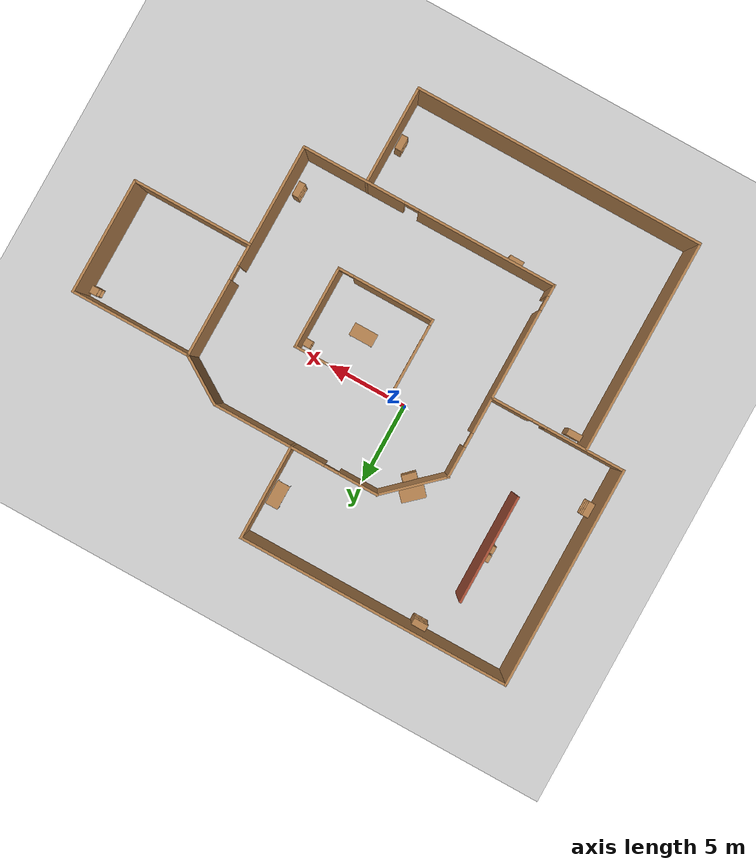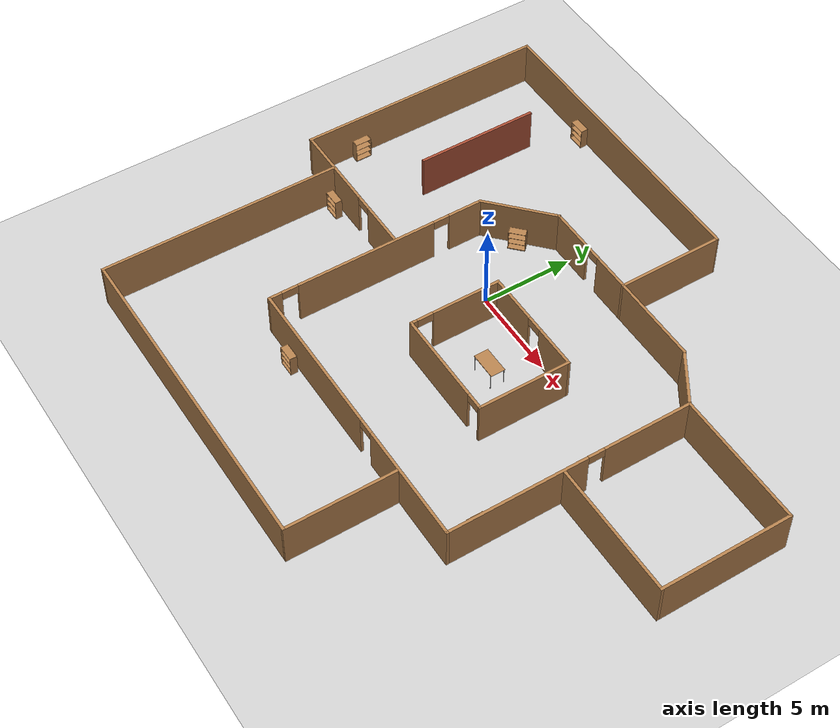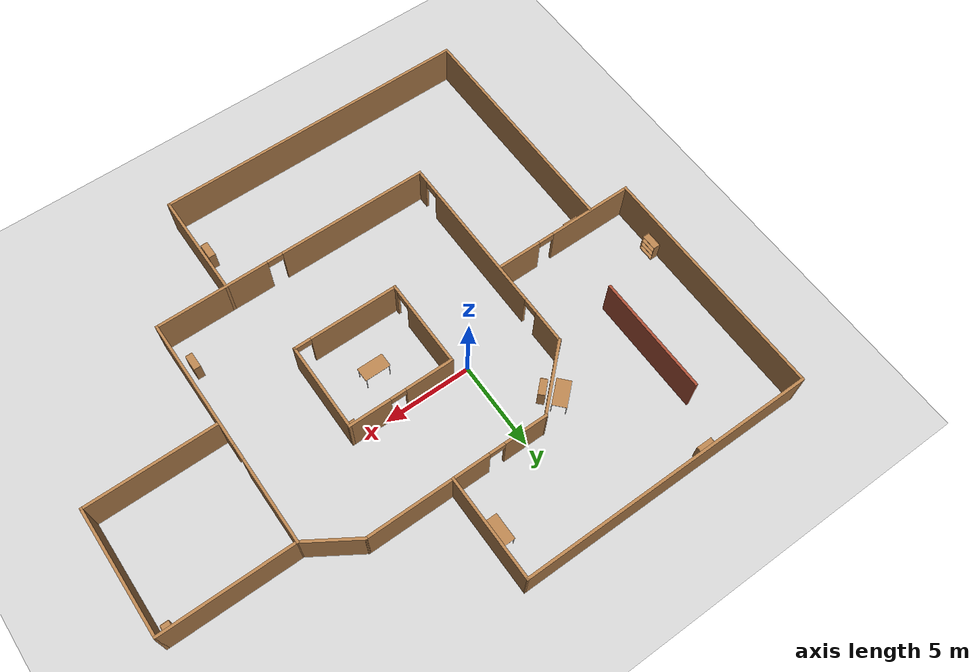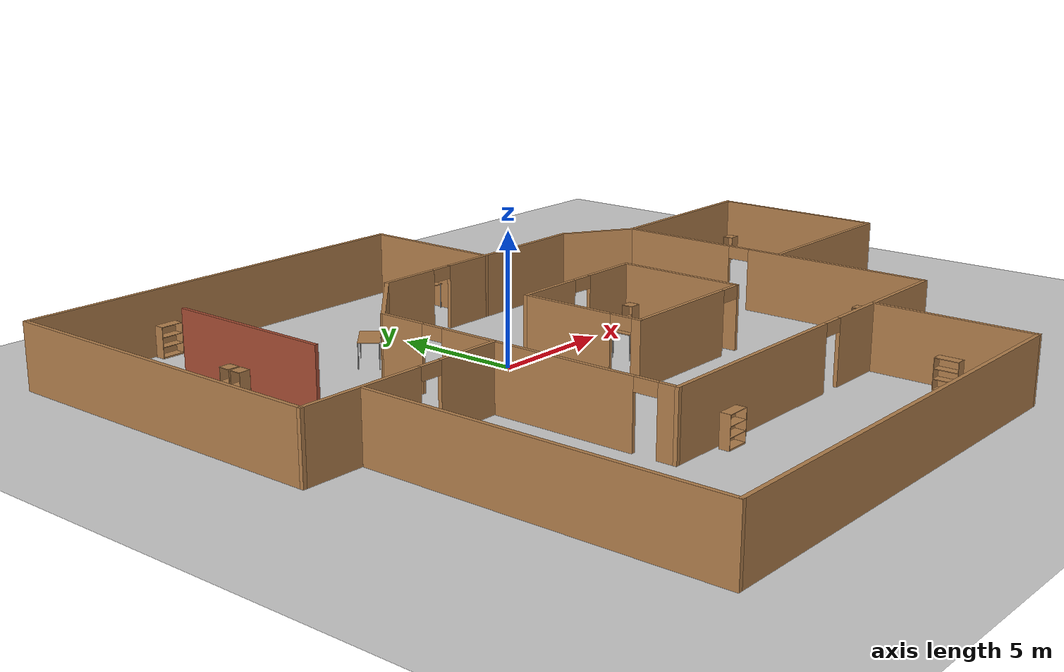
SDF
<sdf version="1.7">
 <world name="default">
  <light name="sun" type="directional">
   <pose>0 0 10 0 -0 0</pose>
   <diffuse>0.8 0.8 0.8 1</diffuse>
   <specular>0.2 0.2 0.2 1</specular>
   <attenuation>
    <range>1000</range>
    <constant>0.9</constant>
    <linear>0.01</linear>
    <quadratic>0.001</quadratic>
   </attenuation>
   <direction>-0.5 0.1 -0.9</direction>
   <spot><inner_angle>0</inner_angle><outer_angle>0</outer_angle><falloff>0</falloff></spot>
  </light>
  <model name="ground_plane">
   <static>1</static>
   <link name="link">
    <collision name="collision">
     <geometry><plane><normal>0 0 1</normal><size>100 100</size></plane></geometry>
     <surface>
      <contact><collide_bitmask>65535</collide_bitmask></contact>
      <friction><ode><mu>100</mu><mu2>50</mu2></ode></friction>
     </surface>
    </collision>
    <visual name="visual">
     <cast_shadows>0</cast_shadows>
     <geometry><plane><normal>0 0 1</normal><size>100 100</size></plane></geometry>
     <material>
      <script><uri>file://media/materials/scripts/gazebo.material</uri><name>Gazebo/Grey</name></script>
     </material>
    </visual>
   </link>
  </model>
  <gravity>0 0 -9.8</gravity>
  <magnetic_field>6e-06 2.3e-05 -4.2e-05</magnetic_field>
  <atmosphere type="adiabatic"/>
  <physics type="ode">
   <max_step_size>0.001</max_step_size>
   <real_time_factor>1</real_time_factor>
   <real_time_update_rate>1000</real_time_update_rate>
  </physics>
  <scene><ambient>0.4 0.4 0.4 1</ambient><background>0.7 0.7 0.7 1</background><shadows>1</shadows></scene>
  <audio><device>default</device></audio>
  <spherical_coordinates>
   <surface_model>EARTH_WGS84</surface_model>
   <latitude_deg>0</latitude_deg>
   <longitude_deg>0</longitude_deg>
   <elevation>0</elevation>
   <heading_deg>0</heading_deg>
  </spherical_coordinates>
  <model name="rs1_floor_plan_2">
   <pose>3.48266 -2.61019 0 0 -0 0</pose>
   <link name="Wall_1">
    <pose>8.51734 -0.714811 0 0 -0 -1.5708</pose>
    <visual name="Wall_1_Visual_0">
     <pose>-4.28666 0 1.25 0 -0 0</pose>
     <geometry><box><size>4.92668 0.15 2.5</size></box></geometry>
     <material>
      <script><uri>file://media/materials/scripts/gazebo.material</uri><name>Gazebo/Wood</name></script>
      <ambient>1 1 1 1</ambient>
     </material>
     <meta><layer>0</layer></meta>
    </visual>
    <collision name="Wall_1_Collision_0">
     <geometry><box><size>4.92668 0.15 2.5</size></box></geometry>
     <pose>-4.28666 0 1.25 0 -0 0</pose>
    </collision>
    <visual name="Wall_1_Visual_1">
     <pose>2.91334 0 1.25 0 -0 0</pose>
     <geometry><box><size>7.67333 0.15 2.5</size></box></geometry>
     <material>
      <script><uri>file://media/materials/scripts/gazebo.material</uri><name>Gazebo/Wood</name></script>
      <ambient>1 1 1 1</ambient>
     </material>
     <meta><layer>0</layer></meta>
    </visual>
    <collision name="Wall_1_Collision_1">
     <geometry><box><size>7.67333 0.15 2.5</size></box></geometry>
     <pose>2.91334 0 1.25 0 -0 0</pose>
    </collision>
    <visual name="Wall_1_Visual_2">
     <pose>-1.37332 0 2.25 0 -0 0</pose>
     <geometry><box><size>0.9 0.15 0.5</size></box></geometry>
     <material>
      <script><uri>file://media/materials/scripts/gazebo.material</uri><name>Gazebo/Wood</name></script>
      <ambient>1 1 1 1</ambient>
     </material>
     <meta><layer>0</layer></meta>
    </visual>
    <collision name="Wall_1_Collision_2">
     <geometry><box><size>0.9 0.15 0.5</size></box></geometry>
     <pose>-1.37332 0 2.25 0 -0 0</pose>
    </collision>
   </link>
   <link name="Wall_11">
    <pose>-11.6939 -0.210359 0 0 -0 3.14159</pose>
    <visual name="Wall_11_Visual_0">
     <pose>-2.93535 0 1.25 0 -0 0</pose>
     <geometry><box><size>2.6293 0.15 2.5</size></box></geometry>
     <material>
      <script><uri>file://media/materials/scripts/gazebo.material</uri><name>Gazebo/Wood</name></script>
      <ambient>1 1 1 1</ambient>
     </material>
     <meta><layer>0</layer></meta>
    </visual>
    <collision name="Wall_11_Collision_0">
     <geometry><box><size>2.6293 0.15 2.5</size></box></geometry>
     <pose>-2.93535 0 1.25 0 -0 0</pose>
    </collision>
    <visual name="Wall_11_Visual_1">
     <pose>1.76465 0 1.25 0 -0 0</pose>
     <geometry><box><size>4.9707 0.15 2.5</size></box></geometry>
     <material>
      <script><uri>file://media/materials/scripts/gazebo.material</uri><name>Gazebo/Wood</name></script>
      <ambient>1 1 1 1</ambient>
     </material>
     <meta><layer>0</layer></meta>
    </visual>
    <collision name="Wall_11_Collision_1">
     <geometry><box><size>4.9707 0.15 2.5</size></box></geometry>
     <pose>1.76465 0 1.25 0 -0 0</pose>
    </collision>
    <visual name="Wall_11_Visual_2">
     <pose>-1.1707 0 2.25 0 -0 0</pose>
     <geometry><box><size>0.9 0.15 0.5</size></box></geometry>
     <material>
      <script><uri>file://media/materials/scripts/gazebo.material</uri><name>Gazebo/Wood</name></script>
      <ambient>1 1 1 1</ambient>
     </material>
     <meta><layer>0</layer></meta>
    </visual>
    <collision name="Wall_11_Collision_2">
     <geometry><box><size>0.9 0.15 0.5</size></box></geometry>
     <pose>-1.1707 0 2.25 0 -0 0</pose>
    </collision>
   </link>
   <link name="Wall_12">
    <collision name="Wall_12_Collision">
     <geometry><box><size>13.75 0.15 2.5</size></box></geometry>
     <pose>0 0 1.25 0 -0 0</pose>
    </collision>
    <visual name="Wall_12_Visual">
     <pose>0 0 1.25 0 -0 0</pose>
     <geometry><box><size>13.75 0.15 2.5</size></box></geometry>
     <material>
      <script><uri>file://media/materials/scripts/gazebo.material</uri><name>Gazebo/Wood</name></script>
      <ambient>1 1 1 1</ambient>
     </material>
     <meta><layer>0</layer></meta>
    </visual>
    <pose>-15.8689 6.58964 0 0 -0 1.5708</pose>
   </link>
   <link name="Wall_13">
    <collision name="Wall_13_Collision">
     <geometry><box><size>17 0.15 2.5</size></box></geometry>
     <pose>0 0 1.25 0 -0 0</pose>
    </collision>
    <visual name="Wall_13_Visual">
     <pose>0 0 1.25 0 -0 0</pose>
     <geometry><box><size>17 0.15 2.5</size></box></geometry>
     <material>
      <script><uri>file://media/materials/scripts/gazebo.material</uri><name>Gazebo/Wood</name></script>
      <ambient>1 1 1 1</ambient>
     </material>
     <meta><layer>0</layer></meta>
    </visual>
    <pose>-7.44387 13.3896 0 0 -0 0</pose>
   </link>
   <link name="Wall_14">
    <collision name="Wall_14_Collision">
     <geometry><box><size>5.91225 0.15 2.5</size></box></geometry>
     <pose>0 0 1.25 0 -0 0</pose>
    </collision>
    <visual name="Wall_14_Visual">
     <pose>0 0 1.25 0 -0 0</pose>
     <geometry><box><size>5.91225 0.15 2.5</size></box></geometry>
     <material>
      <script><uri>file://media/materials/scripts/gazebo.material</uri><name>Gazebo/Wood</name></script>
      <ambient>1 1 1 1</ambient>
     </material>
     <meta><layer>0</layer></meta>
    </visual>
    <pose>0.987578 10.5085 0 0 -0 -1.56856</pose>
   </link>
   <link name="Wall_16">
    <collision name="Wall_16_Collision">
     <geometry><box><size>7.5 0.15 2.5</size></box></geometry>
     <pose>0 0 1.25 0 -0 0</pose>
    </collision>
    <visual name="Wall_16_Visual">
     <pose>0 0 1.25 0 -0 0</pose>
     <geometry><box><size>7.5 0.15 2.5</size></box></geometry>
     <material>
      <script><uri>file://media/materials/scripts/gazebo.material</uri><name>Gazebo/Wood</name></script>
      <ambient>1 1 1 1</ambient>
     </material>
     <meta><layer>0</layer></meta>
    </visual>
    <pose>12.1939 5.958 0 0 -0 0</pose>
   </link>
   <link name="Wall_17">
    <collision name="Wall_17_Collision">
     <geometry><box><size>7.25 0.15 2.5</size></box></geometry>
     <pose>0 0 1.25 0 -0 0</pose>
    </collision>
    <visual name="Wall_17_Visual">
     <pose>0 0 1.25 0 -0 0</pose>
     <geometry><box><size>7.25 0.15 2.5</size></box></geometry>
     <material>
      <script><uri>file://media/materials/scripts/gazebo.material</uri><name>Gazebo/Wood</name></script>
      <ambient>1 1 1 1</ambient>
     </material>
     <meta><layer>0</layer></meta>
    </visual>
    <pose>15.8689 2.408 0 0 -0 -1.5708</pose>
   </link>
   <link name="Wall_18">
    <collision name="Wall_18_Collision">
     <geometry><box><size>7.5 0.15 2.5</size></box></geometry>
     <pose>0 0 1.25 0 -0 0</pose>
    </collision>
    <visual name="Wall_18_Visual">
     <pose>0 0 1.25 0 -0 0</pose>
     <geometry><box><size>7.5 0.15 2.5</size></box></geometry>
     <material>
      <script><uri>file://media/materials/scripts/gazebo.material</uri><name>Gazebo/Wood</name></script>
      <ambient>1 1 1 1</ambient>
     </material>
     <meta><layer>0</layer></meta>
    </visual>
    <pose>12.1939 -1.142 0 0 -0 3.14159</pose>
   </link>
   <link name="Wall_2">
    <pose>0.517338 -7.38981 0 0 -0 3.14159</pose>
    <visual name="Wall_2_Visual_0">
     <pose>-4.8168 0 1.25 0 -0 0</pose>
     <geometry><box><size>6.5164 0.15 2.5</size></box></geometry>
     <material>
      <script><uri>file://media/materials/scripts/gazebo.material</uri><name>Gazebo/Wood</name></script>
      <ambient>1 1 1 1</ambient>
     </material>
     <meta><layer>0</layer></meta>
    </visual>
    <collision name="Wall_2_Collision_0">
     <geometry><box><size>6.5164 0.15 2.5</size></box></geometry>
     <pose>-4.8168 0 1.25 0 -0 0</pose>
    </collision>
    <visual name="Wall_2_Visual_1">
     <pose>3.7082 0 1.25 0 -0 0</pose>
     <geometry><box><size>8.7336 0.15 2.5</size></box></geometry>
     <material>
      <script><uri>file://media/materials/scripts/gazebo.material</uri><name>Gazebo/Wood</name></script>
      <ambient>1 1 1 1</ambient>
     </material>
     <meta><layer>0</layer></meta>
    </visual>
    <collision name="Wall_2_Collision_1">
     <geometry><box><size>8.7336 0.15 2.5</size></box></geometry>
     <pose>3.7082 0 1.25 0 -0 0</pose>
    </collision>
    <visual name="Wall_2_Visual_2">
     <pose>-1.1086 0 2.25 0 -0 0</pose>
     <geometry><box><size>0.9 0.15 0.5</size></box></geometry>
     <material>
      <script><uri>file://media/materials/scripts/gazebo.material</uri><name>Gazebo/Wood</name></script>
      <ambient>1 1 1 1</ambient>
     </material>
     <meta><layer>0</layer></meta>
    </visual>
    <collision name="Wall_2_Collision_2">
     <geometry><box><size>0.9 0.15 0.5</size></box></geometry>
     <pose>-1.1086 0 2.25 0 -0 0</pose>
    </collision>
   </link>
   <link name="Wall_20">
    <collision name="Wall_20_Collision">
     <geometry><box><size>4.25366 0.15 2.5</size></box></geometry>
     <pose>0 0 1.25 0 -0 0</pose>
    </collision>
    <visual name="Wall_20_Visual">
     <pose>0 0 1.25 0 -0 0</pose>
     <geometry><box><size>4.25366 0.15 2.5</size></box></geometry>
     <material>
      <script><uri>file://media/materials/scripts/gazebo.material</uri><name>Gazebo/Wood</name></script>
      <ambient>1 1 1 1</ambient>
     </material>
     <meta><layer>0</layer></meta>
    </visual>
    <pose>-5.98266 6.23019 0 0 -0 0.750929</pose>
   </link>
   <link name="Wall_21">
    <pose>0.702338 7.63019 0 0 -0 0</pose>
    <visual name="Wall_21_Visual_0">
     <pose>-3.9907 0 1.25 0 -0 0</pose>
     <geometry><box><size>2.5386 0.15 2.5</size></box></geometry>
     <material>
      <script><uri>file://media/materials/scripts/gazebo.material</uri><name>Gazebo/Wood</name></script>
      <ambient>1 1 1 1</ambient>
     </material>
     <meta><layer>0</layer></meta>
    </visual>
    <collision name="Wall_21_Collision_0">
     <geometry><box><size>2.5386 0.15 2.5</size></box></geometry>
     <pose>-3.9907 0 1.25 0 -0 0</pose>
    </collision>
    <visual name="Wall_21_Visual_1">
     <pose>1.7193 0 1.25 0 -0 0</pose>
     <geometry><box><size>7.0814 0.15 2.5</size></box></geometry>
     <material>
      <script><uri>file://media/materials/scripts/gazebo.material</uri><name>Gazebo/Wood</name></script>
      <ambient>1 1 1 1</ambient>
     </material>
     <meta><layer>0</layer></meta>
    </visual>
    <collision name="Wall_21_Collision_1">
     <geometry><box><size>7.0814 0.15 2.5</size></box></geometry>
     <pose>1.7193 0 1.25 0 -0 0</pose>
    </collision>
    <visual name="Wall_21_Visual_2">
     <pose>-2.2714 0 2.25 0 -0 0</pose>
     <geometry><box><size>0.9 0.15 0.5</size></box></geometry>
     <material>
      <script><uri>file://media/materials/scripts/gazebo.material</uri><name>Gazebo/Wood</name></script>
      <ambient>1 1 1 1</ambient>
     </material>
     <meta><layer>0</layer></meta>
    </visual>
    <collision name="Wall_21_Collision_2">
     <geometry><box><size>0.9 0.15 0.5</size></box></geometry>
     <pose>-2.2714 0 2.25 0 -0 0</pose>
    </collision>
   </link>
   <link name="Wall_22">
    <collision name="Wall_22_Collision">
     <geometry><box><size>3.26774 0.15 2.5</size></box></geometry>
     <pose>0 0 1.25 0 -0 0</pose>
    </collision>
    <visual name="Wall_22_Visual">
     <pose>0 0 1.25 0 -0 0</pose>
     <geometry><box><size>3.26774 0.15 2.5</size></box></geometry>
     <material>
      <script><uri>file://media/materials/scripts/gazebo.material</uri><name>Gazebo/Wood</name></script>
      <ambient>1 1 1 1</ambient>
     </material>
     <meta><layer>0</layer></meta>
    </visual>
    <pose>7.2031 6.79409 0 0 -0 -0.566075</pose>
   </link>
   <link name="Wall_24">
    <collision name="Wall_24_Collision">
     <geometry><box><size>6.75 0.15 2.5</size></box></geometry>
     <pose>0 0 1.25 0 -0 0</pose>
    </collision>
    <visual name="Wall_24_Visual">
     <pose>0 0 1.25 0 -0 0</pose>
     <geometry><box><size>6.75 0.15 2.5</size></box></geometry>
     <material>
      <script><uri>file://media/materials/scripts/gazebo.material</uri><name>Gazebo/Bricks</name></script>
      <ambient>1 1 1 1</ambient>
     </material>
     <meta><layer>0</layer></meta>
    </visual>
    <pose>-11.443 7.26025 0 0 -0 -1.5708</pose>
   </link>
   <link name="Wall_26">
    <collision name="Wall_26_Collision">
     <geometry><box><size>13.25 0.15 2.5</size></box></geometry>
     <pose>0 0 1.25 0 -0 0</pose>
    </collision>
    <visual name="Wall_26_Visual">
     <pose>0 0 1.25 0 -0 0</pose>
     <geometry><box><size>13.25 0.15 2.5</size></box></geometry>
     <material>
      <script><uri>file://media/materials/scripts/gazebo.material</uri><name>Gazebo/Wood</name></script>
      <ambient>1 1 1 1</ambient>
     </material>
     <meta><layer>0</layer></meta>
    </visual>
    <pose>-13.4827 -6.83981 0 0 -0 -1.5708</pose>
   </link>
   <link name="Wall_27">
    <collision name="Wall_27_Collision">
     <geometry><box><size>18.15 0.15 2.5</size></box></geometry>
     <pose>0 0 1.25 0 -0 0</pose>
    </collision>
    <visual name="Wall_27_Visual">
     <pose>0 0 1.25 0 -0 0</pose>
     <geometry><box><size>18.15 0.15 2.5</size></box></geometry>
     <material>
      <script><uri>file://media/materials/scripts/gazebo.material</uri><name>Gazebo/Wood</name></script>
      <ambient>1 1 1 1</ambient>
     </material>
     <meta><layer>0</layer></meta>
    </visual>
    <pose>-4.48266 -13.3898 0 0 -0 0</pose>
   </link>
   <link name="Wall_28">
    <collision name="Wall_28_Collision">
     <geometry><box><size>6.15 0.15 2.5</size></box></geometry>
     <pose>0 0 1.25 0 -0 0</pose>
    </collision>
    <visual name="Wall_28_Visual">
     <pose>0 0 1.25 0 -0 0</pose>
     <geometry><box><size>6.15 0.15 2.5</size></box></geometry>
     <material>
      <script><uri>file://media/materials/scripts/gazebo.material</uri><name>Gazebo/Wood</name></script>
      <ambient>1 1 1 1</ambient>
     </material>
     <meta><layer>0</layer></meta>
    </visual>
    <pose>4.51734 -10.3898 0 0 -0 1.5708</pose>
   </link>
   <link name="Wall_3">
    <pose>-7.48266 -1.27981 0 0 -0 1.5708</pose>
    <visual name="Wall_3_Visual_0">
     <pose>-5.80672 0 1.25 0 -0 0</pose>
     <geometry><box><size>0.756566 0.15 2.5</size></box></geometry>
     <material>
      <script><uri>file://media/materials/scripts/gazebo.material</uri><name>Gazebo/Wood</name></script>
      <ambient>1 1 1 1</ambient>
     </material>
     <meta><layer>0</layer></meta>
    </visual>
    <collision name="Wall_3_Collision_0">
     <geometry><box><size>0.756566 0.15 2.5</size></box></geometry>
     <pose>-5.80672 0 1.25 0 -0 0</pose>
    </collision>
    <visual name="Wall_3_Visual_1">
     <pose>-0.606396 0 1.25 0 -0 0</pose>
     <geometry><box><size>7.84408 0.15 2.5</size></box></geometry>
     <material>
      <script><uri>file://media/materials/scripts/gazebo.material</uri><name>Gazebo/Wood</name></script>
      <ambient>1 1 1 1</ambient>
     </material>
     <meta><layer>0</layer></meta>
    </visual>
    <collision name="Wall_3_Collision_1">
     <geometry><box><size>7.84408 0.15 2.5</size></box></geometry>
     <pose>-0.606396 0 1.25 0 -0 0</pose>
    </collision>
    <visual name="Wall_3_Visual_2">
     <pose>5.20032 0 1.25 0 -0 0</pose>
     <geometry><box><size>1.96936 0.15 2.5</size></box></geometry>
     <material>
      <script><uri>file://media/materials/scripts/gazebo.material</uri><name>Gazebo/Wood</name></script>
      <ambient>1 1 1 1</ambient>
     </material>
     <meta><layer>0</layer></meta>
    </visual>
    <collision name="Wall_3_Collision_2">
     <geometry><box><size>1.96936 0.15 2.5</size></box></geometry>
     <pose>5.20032 0 1.25 0 -0 0</pose>
    </collision>
    <visual name="Wall_3_Visual_3">
     <pose>-4.97843 0 2.25 0 -0 0</pose>
     <geometry><box><size>0.9 0.15 0.5</size></box></geometry>
     <material>
      <script><uri>file://media/materials/scripts/gazebo.material</uri><name>Gazebo/Wood</name></script>
      <ambient>1 1 1 1</ambient>
     </material>
     <meta><layer>0</layer></meta>
    </visual>
    <collision name="Wall_3_Collision_3">
     <geometry><box><size>0.9 0.15 0.5</size></box></geometry>
     <pose>-4.97843 0 2.25 0 -0 0</pose>
    </collision>
    <visual name="Wall_3_Visual_4">
     <pose>3.76564 0 2.25 0 -0 0</pose>
     <geometry><box><size>0.9 0.15 0.5</size></box></geometry>
     <material>
      <script><uri>file://media/materials/scripts/gazebo.material</uri><name>Gazebo/Wood</name></script>
      <ambient>1 1 1 1</ambient>
     </material>
     <meta><layer>0</layer></meta>
    </visual>
    <collision name="Wall_3_Collision_4">
     <geometry><box><size>0.9 0.15 0.5</size></box></geometry>
     <pose>3.76564 0 2.25 0 -0 0</pose>
    </collision>
   </link>
   <link name="Wall_5">
    <pose>-2.48266 0.110189 0 0 -0 -1.5708</pose>
    <visual name="Wall_5_Visual_0">
     <pose>-0.647016 0 1.25 0 -0 0</pose>
     <geometry><box><size>3.85597 0.15 2.5</size></box></geometry>
     <material>
      <script><uri>file://media/materials/scripts/gazebo.material</uri><name>Gazebo/Wood</name></script>
      <ambient>1 1 1 1</ambient>
     </material>
     <meta><layer>0</layer></meta>
    </visual>
    <collision name="Wall_5_Collision_0">
     <geometry><box><size>3.85597 0.15 2.5</size></box></geometry>
     <pose>-0.647016 0 1.25 0 -0 0</pose>
    </collision>
    <visual name="Wall_5_Visual_1">
     <pose>2.37798 0 1.25 0 -0 0</pose>
     <geometry><box><size>0.394033 0.15 2.5</size></box></geometry>
     <material>
      <script><uri>file://media/materials/scripts/gazebo.material</uri><name>Gazebo/Wood</name></script>
      <ambient>1 1 1 1</ambient>
     </material>
     <meta><layer>0</layer></meta>
    </visual>
    <collision name="Wall_5_Collision_1">
     <geometry><box><size>0.394033 0.15 2.5</size></box></geometry>
     <pose>2.37798 0 1.25 0 -0 0</pose>
    </collision>
    <visual name="Wall_5_Visual_2">
     <pose>1.73097 0 2.25 0 -0 0</pose>
     <geometry><box><size>0.9 0.15 0.5</size></box></geometry>
     <material>
      <script><uri>file://media/materials/scripts/gazebo.material</uri><name>Gazebo/Wood</name></script>
      <ambient>1 1 1 1</ambient>
     </material>
     <meta><layer>0</layer></meta>
    </visual>
    <collision name="Wall_5_Collision_2">
     <geometry><box><size>0.9 0.15 0.5</size></box></geometry>
     <pose>1.73097 0 2.25 0 -0 0</pose>
    </collision>
   </link>
   <link name="Wall_6">
    <pose>0.517338 -2.38981 0 0 -0 0</pose>
    <visual name="Wall_6_Visual_0">
     <pose>-0.506158 0 1.25 0 -0 0</pose>
     <geometry><box><size>5.13769 0.15 2.5</size></box></geometry>
     <material>
      <script><uri>file://media/materials/scripts/gazebo.material</uri><name>Gazebo/Wood</name></script>
      <ambient>1 1 1 1</ambient>
     </material>
     <meta><layer>0</layer></meta>
    </visual>
    <collision name="Wall_6_Collision_0">
     <geometry><box><size>5.13769 0.15 2.5</size></box></geometry>
     <pose>-0.506158 0 1.25 0 -0 0</pose>
    </collision>
    <visual name="Wall_6_Visual_1">
     <pose>3.01884 0 1.25 0 -0 0</pose>
     <geometry><box><size>0.112315 0.15 2.5</size></box></geometry>
     <material>
      <script><uri>file://media/materials/scripts/gazebo.material</uri><name>Gazebo/Wood</name></script>
      <ambient>1 1 1 1</ambient>
     </material>
     <meta><layer>0</layer></meta>
    </visual>
    <collision name="Wall_6_Collision_1">
     <geometry><box><size>0.112315 0.15 2.5</size></box></geometry>
     <pose>3.01884 0 1.25 0 -0 0</pose>
    </collision>
    <visual name="Wall_6_Visual_2">
     <pose>2.51268 0 2.25 0 -0 0</pose>
     <geometry><box><size>0.9 0.15 0.5</size></box></geometry>
     <material>
      <script><uri>file://media/materials/scripts/gazebo.material</uri><name>Gazebo/Wood</name></script>
      <ambient>1 1 1 1</ambient>
     </material>
     <meta><layer>0</layer></meta>
    </visual>
    <collision name="Wall_6_Collision_2">
     <geometry><box><size>0.9 0.15 0.5</size></box></geometry>
     <pose>2.51268 0 2.25 0 -0 0</pose>
    </collision>
   </link>
   <link name="Wall_7">
    <collision name="Wall_7_Collision">
     <geometry><box><size>5.15 0.15 2.5</size></box></geometry>
     <pose>0 0 1.25 0 -0 0</pose>
    </collision>
    <visual name="Wall_7_Visual">
     <pose>0 0 1.25 0 -0 0</pose>
     <geometry><box><size>5.15 0.15 2.5</size></box></geometry>
     <material>
      <script><uri>file://media/materials/scripts/gazebo.material</uri><name>Gazebo/Wood</name></script>
      <ambient>1 1 1 1</ambient>
     </material>
     <meta><layer>0</layer></meta>
    </visual>
    <pose>3.51734 0.110189 0 0 -0 1.5708</pose>
   </link>
   <link name="Wall_8">
    <pose>0.517338 2.61019 0 0 -0 3.14159</pose>
    <visual name="Wall_8_Visual_0">
     <pose>-1.85331 0 1.25 0 -0 0</pose>
     <geometry><box><size>2.44338 0.15 2.5</size></box></geometry>
     <material>
      <script><uri>file://media/materials/scripts/gazebo.material</uri><name>Gazebo/Wood</name></script>
      <ambient>1 1 1 1</ambient>
     </material>
     <meta><layer>0</layer></meta>
    </visual>
    <collision name="Wall_8_Collision_0">
     <geometry><box><size>2.44338 0.15 2.5</size></box></geometry>
     <pose>-1.85331 0 1.25 0 -0 0</pose>
    </collision>
    <visual name="Wall_8_Visual_1">
     <pose>1.67169 0 1.25 0 -0 0</pose>
     <geometry><box><size>2.80662 0.15 2.5</size></box></geometry>
     <material>
      <script><uri>file://media/materials/scripts/gazebo.material</uri><name>Gazebo/Wood</name></script>
      <ambient>1 1 1 1</ambient>
     </material>
     <meta><layer>0</layer></meta>
    </visual>
    <collision name="Wall_8_Collision_1">
     <geometry><box><size>2.80662 0.15 2.5</size></box></geometry>
     <pose>1.67169 0 1.25 0 -0 0</pose>
    </collision>
    <visual name="Wall_8_Visual_2">
     <pose>-0.181616 0 2.25 0 -0 0</pose>
     <geometry><box><size>0.9 0.15 0.5</size></box></geometry>
     <material>
      <script><uri>file://media/materials/scripts/gazebo.material</uri><name>Gazebo/Wood</name></script>
      <ambient>1 1 1 1</ambient>
     </material>
     <meta><layer>0</layer></meta>
    </visual>
    <collision name="Wall_8_Collision_2">
     <geometry><box><size>0.9 0.15 0.5</size></box></geometry>
     <pose>-0.181616 0 2.25 0 -0 0</pose>
    </collision>
   </link>
   <static>1</static>
  </model>
  <model name="table">
   <static>1</static>
   <link name="link">
    <collision name="surface">
     <pose>0 0 1 0 -0 0</pose>
     <geometry><box><size>1.5 0.8 0.03</size></box></geometry>
     <surface><friction><ode><mu>0.6</mu><mu2>0.6</mu2></ode></friction></surface>
    </collision>
    <visual name="visual1">
     <pose>0 0 1 0 -0 0</pose>
     <geometry><box><size>1.5 0.8 0.03</size></box></geometry>
     <material>
      <script><uri>file://media/materials/scripts/gazebo.material</uri><name>Gazebo/Wood</name></script>
     </material>
    </visual>
    <collision name="front_left_leg">
     <pose>0.68 0.38 0.5 0 -0 0</pose>
     <geometry><cylinder><radius>0.02</radius><length>1</length></cylinder></geometry>
    </collision>
    <visual name="front_left_leg">
     <pose>0.68 0.38 0.5 0 -0 0</pose>
     <geometry><cylinder><radius>0.02</radius><length>1</length></cylinder></geometry>
     <material>
      <script><uri>file://media/materials/scripts/gazebo.material</uri><name>Gazebo/Grey</name></script>
     </material>
    </visual>
    <collision name="front_right_leg">
     <pose>0.68 -0.38 0.5 0 -0 0</pose>
     <geometry><cylinder><radius>0.02</radius><length>1</length></cylinder></geometry>
    </collision>
    <visual name="front_right_leg">
     <pose>0.68 -0.38 0.5 0 -0 0</pose>
     <geometry><cylinder><radius>0.02</radius><length>1</length></cylinder></geometry>
     <material>
      <script><uri>file://media/materials/scripts/gazebo.material</uri><name>Gazebo/Grey</name></script>
     </material>
    </visual>
    <collision name="back_right_leg">
     <pose>-0.68 -0.38 0.5 0 -0 0</pose>
     <geometry><cylinder><radius>0.02</radius><length>1</length></cylinder></geometry>
    </collision>
    <visual name="back_right_leg">
     <pose>-0.68 -0.38 0.5 0 -0 0</pose>
     <geometry><cylinder><radius>0.02</radius><length>1</length></cylinder></geometry>
     <material>
      <script><uri>file://media/materials/scripts/gazebo.material</uri><name>Gazebo/Grey</name></script>
     </material>
    </visual>
    <collision name="back_left_leg">
     <pose>-0.68 0.38 0.5 0 -0 0</pose>
     <geometry><cylinder><radius>0.02</radius><length>1</length></cylinder></geometry>
    </collision>
    <visual name="back_left_leg">
     <pose>-0.68 0.38 0.5 0 -0 0</pose>
     <geometry><cylinder><radius>0.02</radius><length>1</length></cylinder></geometry>
     <material>
      <script><uri>file://media/materials/scripts/gazebo.material</uri><name>Gazebo/Grey</name></script>
     </material>
    </visual>
   </link>
   <pose>4.06798 -2.48415 0 0 -0 0</pose>
  </model>
  <model name="table_0">
   <static>1</static>
   <link name="link">
    <collision name="surface">
     <pose>0 0 1 0 -0 0</pose>
     <geometry><box><size>1.5 0.8 0.03</size></box></geometry>
     <surface><friction><ode><mu>0.6</mu><mu2>0.6</mu2></ode></friction></surface>
    </collision>
    <visual name="visual1">
     <pose>0 0 1 0 -0 0</pose>
     <geometry><box><size>1.5 0.8 0.03</size></box></geometry>
     <material>
      <script><uri>file://media/materials/scripts/gazebo.material</uri><name>Gazebo/Wood</name></script>
     </material>
    </visual>
    <collision name="front_left_leg">
     <pose>0.68 0.38 0.5 0 -0 0</pose>
     <geometry><cylinder><radius>0.02</radius><length>1</length></cylinder></geometry>
    </collision>
    <visual name="front_left_leg">
     <pose>0.68 0.38 0.5 0 -0 0</pose>
     <geometry><cylinder><radius>0.02</radius><length>1</length></cylinder></geometry>
     <material>
      <script><uri>file://media/materials/scripts/gazebo.material</uri><name>Gazebo/Grey</name></script>
     </material>
    </visual>
    <collision name="front_right_leg">
     <pose>0.68 -0.38 0.5 0 -0 0</pose>
     <geometry><cylinder><radius>0.02</radius><length>1</length></cylinder></geometry>
    </collision>
    <visual name="front_right_leg">
     <pose>0.68 -0.38 0.5 0 -0 0</pose>
     <geometry><cylinder><radius>0.02</radius><length>1</length></cylinder></geometry>
     <material>
      <script><uri>file://media/materials/scripts/gazebo.material</uri><name>Gazebo/Grey</name></script>
     </material>
    </visual>
    <collision name="back_right_leg">
     <pose>-0.68 -0.38 0.5 0 -0 0</pose>
     <geometry><cylinder><radius>0.02</radius><length>1</length></cylinder></geometry>
    </collision>
    <visual name="back_right_leg">
     <pose>-0.68 -0.38 0.5 0 -0 0</pose>
     <geometry><cylinder><radius>0.02</radius><length>1</length></cylinder></geometry>
     <material>
      <script><uri>file://media/materials/scripts/gazebo.material</uri><name>Gazebo/Grey</name></script>
     </material>
    </visual>
    <collision name="back_left_leg">
     <pose>-0.68 0.38 0.5 0 -0 0</pose>
     <geometry><cylinder><radius>0.02</radius><length>1</length></cylinder></geometry>
    </collision>
    <visual name="back_left_leg">
     <pose>-0.68 0.38 0.5 0 -0 0</pose>
     <geometry><cylinder><radius>0.02</radius><length>1</length></cylinder></geometry>
     <material>
      <script><uri>file://media/materials/scripts/gazebo.material</uri><name>Gazebo/Grey</name></script>
     </material>
    </visual>
   </link>
   <pose>-2.82776 4.12603 0 0 -0 0.737658</pose>
  </model>
  <model name="table_1">
   <static>1</static>
   <link name="link">
    <collision name="surface">
     <pose>0 0 1 0 -0 0</pose>
     <geometry><box><size>1.5 0.8 0.03</size></box></geometry>
     <surface><friction><ode><mu>0.6</mu><mu2>0.6</mu2></ode></friction></surface>
    </collision>
    <visual name="visual1">
     <pose>0 0 1 0 -0 0</pose>
     <geometry><box><size>1.5 0.8 0.03</size></box></geometry>
     <material>
      <script><uri>file://media/materials/scripts/gazebo.material</uri><name>Gazebo/Wood</name></script>
     </material>
    </visual>
    <collision name="front_left_leg">
     <pose>0.68 0.38 0.5 0 -0 0</pose>
     <geometry><cylinder><radius>0.02</radius><length>1</length></cylinder></geometry>
    </collision>
    <visual name="front_left_leg">
     <pose>0.68 0.38 0.5 0 -0 0</pose>
     <geometry><cylinder><radius>0.02</radius><length>1</length></cylinder></geometry>
     <material>
      <script><uri>file://media/materials/scripts/gazebo.material</uri><name>Gazebo/Grey</name></script>
     </material>
    </visual>
    <collision name="front_right_leg">
     <pose>0.68 -0.38 0.5 0 -0 0</pose>
     <geometry><cylinder><radius>0.02</radius><length>1</length></cylinder></geometry>
    </collision>
    <visual name="front_right_leg">
     <pose>0.68 -0.38 0.5 0 -0 0</pose>
     <geometry><cylinder><radius>0.02</radius><length>1</length></cylinder></geometry>
     <material>
      <script><uri>file://media/materials/scripts/gazebo.material</uri><name>Gazebo/Grey</name></script>
     </material>
    </visual>
    <collision name="back_right_leg">
     <pose>-0.68 -0.38 0.5 0 -0 0</pose>
     <geometry><cylinder><radius>0.02</radius><length>1</length></cylinder></geometry>
    </collision>
    <visual name="back_right_leg">
     <pose>-0.68 -0.38 0.5 0 -0 0</pose>
     <geometry><cylinder><radius>0.02</radius><length>1</length></cylinder></geometry>
     <material>
      <script><uri>file://media/materials/scripts/gazebo.material</uri><name>Gazebo/Grey</name></script>
     </material>
    </visual>
    <collision name="back_left_leg">
     <pose>-0.68 0.38 0.5 0 -0 0</pose>
     <geometry><cylinder><radius>0.02</radius><length>1</length></cylinder></geometry>
    </collision>
    <visual name="back_left_leg">
     <pose>-0.68 0.38 0.5 0 -0 0</pose>
     <geometry><cylinder><radius>0.02</radius><length>1</length></cylinder></geometry>
     <material>
      <script><uri>file://media/materials/scripts/gazebo.material</uri><name>Gazebo/Grey</name></script>
     </material>
    </visual>
   </link>
   <pose>3.90488 7.95027 0 0 0 -1.5708</pose>
  </model>
  <model name="bookshelf">
   <static>1</static>
   <link name="link">
    <inertial><mass>1</mass></inertial>
    <collision name="back">
     <pose>0 0.005 0.6 0 -0 0</pose>
     <geometry><box><size>0.9 0.01 1.2</size></box></geometry>
    </collision>
    <visual name="visual1">
     <pose>0 0.005 0.6 0 -0 0</pose>
     <geometry><box><size>0.9 0.01 1.2</size></box></geometry>
     <material>
      <script><uri>file://media/materials/scripts/gazebo.material</uri><name>Gazebo/Wood</name></script>
     </material>
    </visual>
    <collision name="left_side">
     <pose>0.45 -0.195 0.6 0 -0 0</pose>
     <geometry><box><size>0.02 0.4 1.2</size></box></geometry>
    </collision>
    <visual name="visual2">
     <pose>0.45 -0.195 0.6 0 -0 0</pose>
     <geometry><box><size>0.02 0.4 1.2</size></box></geometry>
     <material>
      <script><uri>file://media/materials/scripts/gazebo.material</uri><name>Gazebo/Wood</name></script>
     </material>
    </visual>
    <collision name="right_side">
     <pose>-0.45 -0.195 0.6 0 -0 0</pose>
     <geometry><box><size>0.02 0.4 1.2</size></box></geometry>
    </collision>
    <visual name="visual3">
     <pose>-0.45 -0.195 0.6 0 -0 0</pose>
     <geometry><box><size>0.02 0.4 1.2</size></box></geometry>
     <material>
      <script><uri>file://media/materials/scripts/gazebo.material</uri><name>Gazebo/Wood</name></script>
     </material>
    </visual>
    <collision name="bottom">
     <pose>0 -0.195 0.03 0 -0 0</pose>
     <geometry><box><size>0.88 0.4 0.06</size></box></geometry>
    </collision>
    <visual name="visual4">
     <pose>0 -0.195 0.03 0 -0 0</pose>
     <geometry><box><size>0.88 0.4 0.06</size></box></geometry>
     <material>
      <script><uri>file://media/materials/scripts/gazebo.material</uri><name>Gazebo/Wood</name></script>
     </material>
    </visual>
    <collision name="top">
     <pose>0 -0.195 1.19 0 -0 0</pose>
     <geometry><box><size>0.88 0.4 0.02</size></box></geometry>
    </collision>
    <visual name="visual5">
     <pose>0 -0.195 1.19 0 -0 0</pose>
     <geometry><box><size>0.88 0.4 0.02</size></box></geometry>
     <material>
      <script><uri>file://media/materials/scripts/gazebo.material</uri><name>Gazebo/Wood</name></script>
     </material>
    </visual>
    <collision name="low_shelf">
     <pose>0 -0.195 0.43 0 -0 0</pose>
     <geometry><box><size>0.88 0.4 0.02</size></box></geometry>
    </collision>
    <visual name="visual6">
     <pose>0 -0.195 0.43 0 -0 0</pose>
     <geometry><box><size>0.88 0.4 0.02</size></box></geometry>
     <material>
      <script><uri>file://media/materials/scripts/gazebo.material</uri><name>Gazebo/Wood</name></script>
     </material>
    </visual>
    <collision name="high_shelf">
     <pose>0 -0.195 0.8 0 -0 0</pose>
     <geometry><box><size>0.88 0.4 0.02</size></box></geometry>
    </collision>
    <visual name="visual7">
     <pose>0 -0.195 0.8 0 -0 0</pose>
     <geometry><box><size>0.88 0.4 0.02</size></box></geometry>
     <material>
      <script><uri>file://media/materials/scripts/gazebo.material</uri><name>Gazebo/Wood</name></script>
     </material>
    </visual>
   </link>
   <pose>-6.80218 10.649 0 0 -0 0</pose>
  </model>
  <model name="bookshelf_0">
   <static>1</static>
   <link name="link">
    <inertial><mass>1</mass></inertial>
    <collision name="back">
     <pose>0 0.005 0.6 0 -0 0</pose>
     <geometry><box><size>0.9 0.01 1.2</size></box></geometry>
    </collision>
    <visual name="visual1">
     <pose>0 0.005 0.6 0 -0 0</pose>
     <geometry><box><size>0.9 0.01 1.2</size></box></geometry>
     <material>
      <script><uri>file://media/materials/scripts/gazebo.material</uri><name>Gazebo/Wood</name></script>
     </material>
    </visual>
    <collision name="left_side">
     <pose>0.45 -0.195 0.6 0 -0 0</pose>
     <geometry><box><size>0.02 0.4 1.2</size></box></geometry>
    </collision>
    <visual name="visual2">
     <pose>0.45 -0.195 0.6 0 -0 0</pose>
     <geometry><box><size>0.02 0.4 1.2</size></box></geometry>
     <material>
      <script><uri>file://media/materials/scripts/gazebo.material</uri><name>Gazebo/Wood</name></script>
     </material>
    </visual>
    <collision name="right_side">
     <pose>-0.45 -0.195 0.6 0 -0 0</pose>
     <geometry><box><size>0.02 0.4 1.2</size></box></geometry>
    </collision>
    <visual name="visual3">
     <pose>-0.45 -0.195 0.6 0 -0 0</pose>
     <geometry><box><size>0.02 0.4 1.2</size></box></geometry>
     <material>
      <script><uri>file://media/materials/scripts/gazebo.material</uri><name>Gazebo/Wood</name></script>
     </material>
    </visual>
    <collision name="bottom">
     <pose>0 -0.195 0.03 0 -0 0</pose>
     <geometry><box><size>0.88 0.4 0.06</size></box></geometry>
    </collision>
    <visual name="visual4">
     <pose>0 -0.195 0.03 0 -0 0</pose>
     <geometry><box><size>0.88 0.4 0.06</size></box></geometry>
     <material>
      <script><uri>file://media/materials/scripts/gazebo.material</uri><name>Gazebo/Wood</name></script>
     </material>
    </visual>
    <collision name="top">
     <pose>0 -0.195 1.19 0 -0 0</pose>
     <geometry><box><size>0.88 0.4 0.02</size></box></geometry>
    </collision>
    <visual name="visual5">
     <pose>0 -0.195 1.19 0 -0 0</pose>
     <geometry><box><size>0.88 0.4 0.02</size></box></geometry>
     <material>
      <script><uri>file://media/materials/scripts/gazebo.material</uri><name>Gazebo/Wood</name></script>
     </material>
    </visual>
    <collision name="low_shelf">
     <pose>0 -0.195 0.43 0 -0 0</pose>
     <geometry><box><size>0.88 0.4 0.02</size></box></geometry>
    </collision>
    <visual name="visual6">
     <pose>0 -0.195 0.43 0 -0 0</pose>
     <geometry><box><size>0.88 0.4 0.02</size></box></geometry>
     <material>
      <script><uri>file://media/materials/scripts/gazebo.material</uri><name>Gazebo/Wood</name></script>
     </material>
    </visual>
    <collision name="high_shelf">
     <pose>0 -0.195 0.8 0 -0 0</pose>
     <geometry><box><size>0.88 0.4 0.02</size></box></geometry>
    </collision>
    <visual name="visual7">
     <pose>0 -0.195 0.8 0 -0 0</pose>
     <geometry><box><size>0.88 0.4 0.02</size></box></geometry>
     <material>
      <script><uri>file://media/materials/scripts/gazebo.material</uri><name>Gazebo/Wood</name></script>
     </material>
    </visual>
   </link>
   <pose>-12.257 0.022528 0 0 -0 1.5708</pose>
  </model>
  <model name="cabinet">
   <static>1</static>
   <link name="cabinet_bottom_plate">
    <inertial>
     <pose>0 0 -1 0 -0 0</pose>
     <inertia><ixx>2.05</ixx><ixy>0</ixy><ixz>0</ixz><iyy>2.05</iyy><iyz>0</iyz><izz>2.05</izz></inertia>
     <mass>25</mass>
    </inertial>
    <collision name="cabinet_bottom_plate_geom">
     <pose>0 0 0.01 0 -0 0</pose>
     <geometry><box><size>0.45 0.45 0.02</size></box></geometry>
    </collision>
    <visual name="cabinet_bottom_plate_geom_visual">
     <pose>0 0 0.01 0 -0 0</pose>
     <geometry><box><size>0.45 0.45 0.02</size></box></geometry>
     <material>
      <script><uri>file://media/materials/scripts/gazebo.material</uri><name>Gazebo/Wood</name></script>
     </material>
    </visual>
    <collision name="cabinet_bottom_plate_geom_cabinet_back_plate">
     <pose>0.235 0 0.51 0 -0 0</pose>
     <geometry><box><size>0.02 0.45 1.02</size></box></geometry>
    </collision>
    <visual name="cabinet_bottom_plate_geom_cabinet_back_plate_visual">
     <pose>0.235 0 0.51 0 -0 0</pose>
     <geometry><box><size>0.02 0.45 1.02</size></box></geometry>
     <material>
      <script><uri>file://media/materials/scripts/gazebo.material</uri><name>Gazebo/Wood</name></script>
     </material>
    </visual>
    <collision name="cabinet_bottom_plate_geom_cabinet_left_plate">
     <pose>0 0.235 0.51 0 -0 0</pose>
     <geometry><box><size>0.45 0.02 1.02</size></box></geometry>
    </collision>
    <visual name="cabinet_bottom_plate_geom_cabinet_left_plate_visual">
     <pose>0 0.235 0.51 0 -0 0</pose>
     <geometry><box><size>0.45 0.02 1.02</size></box></geometry>
     <material>
      <script><uri>file://media/materials/scripts/gazebo.material</uri><name>Gazebo/Wood</name></script>
     </material>
    </visual>
    <collision name="cabinet_bottom_plate_geom_cabinet_middle_plate">
     <pose>0 0 0.51 0 -0 0</pose>
     <geometry><box><size>0.45 0.45 0.02</size></box></geometry>
    </collision>
    <visual name="cabinet_bottom_plate_geom_cabinet_middle_plate_visual">
     <pose>0 0 0.51 0 -0 0</pose>
     <geometry><box><size>0.45 0.45 0.02</size></box></geometry>
     <material>
      <script><uri>file://media/materials/scripts/gazebo.material</uri><name>Gazebo/Wood</name></script>
     </material>
    </visual>
    <collision name="cabinet_bottom_plate_geom_cabinet_right_plate">
     <pose>0 -0.235 0.51 0 -0 0</pose>
     <geometry><box><size>0.45 0.02 1.02</size></box></geometry>
    </collision>
    <visual name="cabinet_bottom_plate_geom_cabinet_right_plate_visual">
     <pose>0 -0.235 0.51 0 -0 0</pose>
     <geometry><box><size>0.45 0.02 1.02</size></box></geometry>
     <material>
      <script><uri>file://media/materials/scripts/gazebo.material</uri><name>Gazebo/Wood</name></script>
     </material>
    </visual>
    <collision name="cabinet_bottom_plate_geom_cabinet_top_plate">
     <pose>0 0 1.01 0 -0 0</pose>
     <geometry><box><size>0.45 0.45 0.02</size></box></geometry>
    </collision>
    <visual name="cabinet_bottom_plate_geom_cabinet_top_plate_visual">
     <pose>0 0 1.01 0 -0 0</pose>
     <geometry><box><size>0.45 0.45 0.02</size></box></geometry>
     <material>
      <script><uri>file://media/materials/scripts/gazebo.material</uri><name>Gazebo/Wood</name></script>
     </material>
    </visual>
   </link>
   <pose>6.63594 -0.505404 0 0 -0 0</pose>
  </model>
  <model name="bookshelf_1">
   <static>1</static>
   <link name="link">
    <inertial><mass>1</mass></inertial>
    <collision name="back">
     <pose>0 0.005 0.6 0 -0 0</pose>
     <geometry><box><size>0.9 0.01 1.2</size></box></geometry>
    </collision>
    <visual name="visual1">
     <pose>0 0.005 0.6 0 -0 0</pose>
     <geometry><box><size>0.9 0.01 1.2</size></box></geometry>
     <material>
      <script><uri>file://media/materials/scripts/gazebo.material</uri><name>Gazebo/Wood</name></script>
     </material>
    </visual>
    <collision name="left_side">
     <pose>0.45 -0.195 0.6 0 -0 0</pose>
     <geometry><box><size>0.02 0.4 1.2</size></box></geometry>
    </collision>
    <visual name="visual2">
     <pose>0.45 -0.195 0.6 0 -0 0</pose>
     <geometry><box><size>0.02 0.4 1.2</size></box></geometry>
     <material>
      <script><uri>file://media/materials/scripts/gazebo.material</uri><name>Gazebo/Wood</name></script>
     </material>
    </visual>
    <collision name="right_side">
     <pose>-0.45 -0.195 0.6 0 -0 0</pose>
     <geometry><box><size>0.02 0.4 1.2</size></box></geometry>
    </collision>
    <visual name="visual3">
     <pose>-0.45 -0.195 0.6 0 -0 0</pose>
     <geometry><box><size>0.02 0.4 1.2</size></box></geometry>
     <material>
      <script><uri>file://media/materials/scripts/gazebo.material</uri><name>Gazebo/Wood</name></script>
     </material>
    </visual>
    <collision name="bottom">
     <pose>0 -0.195 0.03 0 -0 0</pose>
     <geometry><box><size>0.88 0.4 0.06</size></box></geometry>
    </collision>
    <visual name="visual4">
     <pose>0 -0.195 0.03 0 -0 0</pose>
     <geometry><box><size>0.88 0.4 0.06</size></box></geometry>
     <material>
      <script><uri>file://media/materials/scripts/gazebo.material</uri><name>Gazebo/Wood</name></script>
     </material>
    </visual>
    <collision name="top">
     <pose>0 -0.195 1.19 0 -0 0</pose>
     <geometry><box><size>0.88 0.4 0.02</size></box></geometry>
    </collision>
    <visual name="visual5">
     <pose>0 -0.195 1.19 0 -0 0</pose>
     <geometry><box><size>0.88 0.4 0.02</size></box></geometry>
     <material>
      <script><uri>file://media/materials/scripts/gazebo.material</uri><name>Gazebo/Wood</name></script>
     </material>
    </visual>
    <collision name="low_shelf">
     <pose>0 -0.195 0.43 0 -0 0</pose>
     <geometry><box><size>0.88 0.4 0.02</size></box></geometry>
    </collision>
    <visual name="visual6">
     <pose>0 -0.195 0.43 0 -0 0</pose>
     <geometry><box><size>0.88 0.4 0.02</size></box></geometry>
     <material>
      <script><uri>file://media/materials/scripts/gazebo.material</uri><name>Gazebo/Wood</name></script>
     </material>
    </visual>
    <collision name="high_shelf">
     <pose>0 -0.195 0.8 0 -0 0</pose>
     <geometry><box><size>0.88 0.4 0.02</size></box></geometry>
    </collision>
    <visual name="visual7">
     <pose>0 -0.195 0.8 0 -0 0</pose>
     <geometry><box><size>0.88 0.4 0.02</size></box></geometry>
     <material>
      <script><uri>file://media/materials/scripts/gazebo.material</uri><name>Gazebo/Wood</name></script>
     </material>
    </visual>
   </link>
   <pose>-9.29234 -3.12068 0 0 -0 0</pose>
  </model>
  <model name="bookshelf_2">
   <static>1</static>
   <link name="link">
    <inertial><mass>1</mass></inertial>
    <collision name="back">
     <pose>0 0.005 0.6 0 -0 0</pose>
     <geometry><box><size>0.9 0.01 1.2</size></box></geometry>
    </collision>
    <visual name="visual1">
     <pose>0 0.005 0.6 0 -0 0</pose>
     <geometry><box><size>0.9 0.01 1.2</size></box></geometry>
     <material>
      <script><uri>file://media/materials/scripts/gazebo.material</uri><name>Gazebo/Wood</name></script>
     </material>
    </visual>
    <collision name="left_side">
     <pose>0.45 -0.195 0.6 0 -0 0</pose>
     <geometry><box><size>0.02 0.4 1.2</size></box></geometry>
    </collision>
    <visual name="visual2">
     <pose>0.45 -0.195 0.6 0 -0 0</pose>
     <geometry><box><size>0.02 0.4 1.2</size></box></geometry>
     <material>
      <script><uri>file://media/materials/scripts/gazebo.material</uri><name>Gazebo/Wood</name></script>
     </material>
    </visual>
    <collision name="right_side">
     <pose>-0.45 -0.195 0.6 0 -0 0</pose>
     <geometry><box><size>0.02 0.4 1.2</size></box></geometry>
    </collision>
    <visual name="visual3">
     <pose>-0.45 -0.195 0.6 0 -0 0</pose>
     <geometry><box><size>0.02 0.4 1.2</size></box></geometry>
     <material>
      <script><uri>file://media/materials/scripts/gazebo.material</uri><name>Gazebo/Wood</name></script>
     </material>
    </visual>
    <collision name="bottom">
     <pose>0 -0.195 0.03 0 -0 0</pose>
     <geometry><box><size>0.88 0.4 0.06</size></box></geometry>
    </collision>
    <visual name="visual4">
     <pose>0 -0.195 0.03 0 -0 0</pose>
     <geometry><box><size>0.88 0.4 0.06</size></box></geometry>
     <material>
      <script><uri>file://media/materials/scripts/gazebo.material</uri><name>Gazebo/Wood</name></script>
     </material>
    </visual>
    <collision name="top">
     <pose>0 -0.195 1.19 0 -0 0</pose>
     <geometry><box><size>0.88 0.4 0.02</size></box></geometry>
    </collision>
    <visual name="visual5">
     <pose>0 -0.195 1.19 0 -0 0</pose>
     <geometry><box><size>0.88 0.4 0.02</size></box></geometry>
     <material>
      <script><uri>file://media/materials/scripts/gazebo.material</uri><name>Gazebo/Wood</name></script>
     </material>
    </visual>
    <collision name="low_shelf">
     <pose>0 -0.195 0.43 0 -0 0</pose>
     <geometry><box><size>0.88 0.4 0.02</size></box></geometry>
    </collision>
    <visual name="visual6">
     <pose>0 -0.195 0.43 0 -0 0</pose>
     <geometry><box><size>0.88 0.4 0.02</size></box></geometry>
     <material>
      <script><uri>file://media/materials/scripts/gazebo.material</uri><name>Gazebo/Wood</name></script>
     </material>
    </visual>
    <collision name="high_shelf">
     <pose>0 -0.195 0.8 0 -0 0</pose>
     <geometry><box><size>0.88 0.4 0.02</size></box></geometry>
    </collision>
    <visual name="visual7">
     <pose>0 -0.195 0.8 0 -0 0</pose>
     <geometry><box><size>0.88 0.4 0.02</size></box></geometry>
     <material>
      <script><uri>file://media/materials/scripts/gazebo.material</uri><name>Gazebo/Wood</name></script>
     </material>
    </visual>
   </link>
   <pose>7.71893 -13.1932 0 0 0 -1.5708</pose>
  </model>
  <model name="bookshelf_3">
   <static>1</static>
   <link name="link">
    <inertial><mass>1</mass></inertial>
    <collision name="back">
     <pose>0 0.005 0.6 0 -0 0</pose>
     <geometry><box><size>0.9 0.01 1.2</size></box></geometry>
    </collision>
    <visual name="visual1">
     <pose>0 0.005 0.6 0 -0 0</pose>
     <geometry><box><size>0.9 0.01 1.2</size></box></geometry>
     <material>
      <script><uri>file://media/materials/scripts/gazebo.material</uri><name>Gazebo/Wood</name></script>
     </material>
    </visual>
    <collision name="left_side">
     <pose>0.45 -0.195 0.6 0 -0 0</pose>
     <geometry><box><size>0.02 0.4 1.2</size></box></geometry>
    </collision>
    <visual name="visual2">
     <pose>0.45 -0.195 0.6 0 -0 0</pose>
     <geometry><box><size>0.02 0.4 1.2</size></box></geometry>
     <material>
      <script><uri>file://media/materials/scripts/gazebo.material</uri><name>Gazebo/Wood</name></script>
     </material>
    </visual>
    <collision name="right_side">
     <pose>-0.45 -0.195 0.6 0 -0 0</pose>
     <geometry><box><size>0.02 0.4 1.2</size></box></geometry>
    </collision>
    <visual name="visual3">
     <pose>-0.45 -0.195 0.6 0 -0 0</pose>
     <geometry><box><size>0.02 0.4 1.2</size></box></geometry>
     <material>
      <script><uri>file://media/materials/scripts/gazebo.material</uri><name>Gazebo/Wood</name></script>
     </material>
    </visual>
    <collision name="bottom">
     <pose>0 -0.195 0.03 0 -0 0</pose>
     <geometry><box><size>0.88 0.4 0.06</size></box></geometry>
    </collision>
    <visual name="visual4">
     <pose>0 -0.195 0.03 0 -0 0</pose>
     <geometry><box><size>0.88 0.4 0.06</size></box></geometry>
     <material>
      <script><uri>file://media/materials/scripts/gazebo.material</uri><name>Gazebo/Wood</name></script>
     </material>
    </visual>
    <collision name="top">
     <pose>0 -0.195 1.19 0 -0 0</pose>
     <geometry><box><size>0.88 0.4 0.02</size></box></geometry>
    </collision>
    <visual name="visual5">
     <pose>0 -0.195 1.19 0 -0 0</pose>
     <geometry><box><size>0.88 0.4 0.02</size></box></geometry>
     <material>
      <script><uri>file://media/materials/scripts/gazebo.material</uri><name>Gazebo/Wood</name></script>
     </material>
    </visual>
    <collision name="low_shelf">
     <pose>0 -0.195 0.43 0 -0 0</pose>
     <geometry><box><size>0.88 0.4 0.02</size></box></geometry>
    </collision>
    <visual name="visual6">
     <pose>0 -0.195 0.43 0 -0 0</pose>
     <geometry><box><size>0.88 0.4 0.02</size></box></geometry>
     <material>
      <script><uri>file://media/materials/scripts/gazebo.material</uri><name>Gazebo/Wood</name></script>
     </material>
    </visual>
    <collision name="high_shelf">
     <pose>0 -0.195 0.8 0 -0 0</pose>
     <geometry><box><size>0.88 0.4 0.02</size></box></geometry>
    </collision>
    <visual name="visual7">
     <pose>0 -0.195 0.8 0 -0 0</pose>
     <geometry><box><size>0.88 0.4 0.02</size></box></geometry>
     <material>
      <script><uri>file://media/materials/scripts/gazebo.material</uri><name>Gazebo/Wood</name></script>
     </material>
    </visual>
   </link>
   <pose>11.567 -7.97815 0 0 0 -1.5708</pose>
  </model>
  <model name="bookshelf_4">
   <static>1</static>
   <link name="link">
    <inertial><mass>1</mass></inertial>
    <collision name="back">
     <pose>0 0.005 0.6 0 -0 0</pose>
     <geometry><box><size>0.9 0.01 1.2</size></box></geometry>
    </collision>
    <visual name="visual1">
     <pose>0 0.005 0.6 0 -0 0</pose>
     <geometry><box><size>0.9 0.01 1.2</size></box></geometry>
     <material>
      <script><uri>file://media/materials/scripts/gazebo.material</uri><name>Gazebo/Wood</name></script>
     </material>
    </visual>
    <collision name="left_side">
     <pose>0.45 -0.195 0.6 0 -0 0</pose>
     <geometry><box><size>0.02 0.4 1.2</size></box></geometry>
    </collision>
    <visual name="visual2">
     <pose>0.45 -0.195 0.6 0 -0 0</pose>
     <geometry><box><size>0.02 0.4 1.2</size></box></geometry>
     <material>
      <script><uri>file://media/materials/scripts/gazebo.material</uri><name>Gazebo/Wood</name></script>
     </material>
    </visual>
    <collision name="right_side">
     <pose>-0.45 -0.195 0.6 0 -0 0</pose>
     <geometry><box><size>0.02 0.4 1.2</size></box></geometry>
    </collision>
    <visual name="visual3">
     <pose>-0.45 -0.195 0.6 0 -0 0</pose>
     <geometry><box><size>0.02 0.4 1.2</size></box></geometry>
     <material>
      <script><uri>file://media/materials/scripts/gazebo.material</uri><name>Gazebo/Wood</name></script>
     </material>
    </visual>
    <collision name="bottom">
     <pose>0 -0.195 0.03 0 -0 0</pose>
     <geometry><box><size>0.88 0.4 0.06</size></box></geometry>
    </collision>
    <visual name="visual4">
     <pose>0 -0.195 0.03 0 -0 0</pose>
     <geometry><box><size>0.88 0.4 0.06</size></box></geometry>
     <material>
      <script><uri>file://media/materials/scripts/gazebo.material</uri><name>Gazebo/Wood</name></script>
     </material>
    </visual>
    <collision name="top">
     <pose>0 -0.195 1.19 0 -0 0</pose>
     <geometry><box><size>0.88 0.4 0.02</size></box></geometry>
    </collision>
    <visual name="visual5">
     <pose>0 -0.195 1.19 0 -0 0</pose>
     <geometry><box><size>0.88 0.4 0.02</size></box></geometry>
     <material>
      <script><uri>file://media/materials/scripts/gazebo.material</uri><name>Gazebo/Wood</name></script>
     </material>
    </visual>
    <collision name="low_shelf">
     <pose>0 -0.195 0.43 0 -0 0</pose>
     <geometry><box><size>0.88 0.4 0.02</size></box></geometry>
    </collision>
    <visual name="visual6">
     <pose>0 -0.195 0.43 0 -0 0</pose>
     <geometry><box><size>0.88 0.4 0.02</size></box></geometry>
     <material>
      <script><uri>file://media/materials/scripts/gazebo.material</uri><name>Gazebo/Wood</name></script>
     </material>
    </visual>
    <collision name="high_shelf">
     <pose>0 -0.195 0.8 0 -0 0</pose>
     <geometry><box><size>0.88 0.4 0.02</size></box></geometry>
    </collision>
    <visual name="visual7">
     <pose>0 -0.195 0.8 0 -0 0</pose>
     <geometry><box><size>0.88 0.4 0.02</size></box></geometry>
     <material>
      <script><uri>file://media/materials/scripts/gazebo.material</uri><name>Gazebo/Wood</name></script>
     </material>
    </visual>
   </link>
   <pose>-1.54199 -10.2049 0 0 -0 0</pose>
  </model>
  <model name="bookshelf_5">
   <static>1</static>
   <link name="link">
    <inertial><mass>1</mass></inertial>
    <collision name="back">
     <pose>0 0.005 0.6 0 -0 0</pose>
     <geometry><box><size>0.9 0.01 1.2</size></box></geometry>
    </collision>
    <visual name="visual1">
     <pose>0 0.005 0.6 0 -0 0</pose>
     <geometry><box><size>0.9 0.01 1.2</size></box></geometry>
     <material>
      <script><uri>file://media/materials/scripts/gazebo.material</uri><name>Gazebo/Wood</name></script>
     </material>
    </visual>
    <collision name="left_side">
     <pose>0.45 -0.195 0.6 0 -0 0</pose>
     <geometry><box><size>0.02 0.4 1.2</size></box></geometry>
    </collision>
    <visual name="visual2">
     <pose>0.45 -0.195 0.6 0 -0 0</pose>
     <geometry><box><size>0.02 0.4 1.2</size></box></geometry>
     <material>
      <script><uri>file://media/materials/scripts/gazebo.material</uri><name>Gazebo/Wood</name></script>
     </material>
    </visual>
    <collision name="right_side">
     <pose>-0.45 -0.195 0.6 0 -0 0</pose>
     <geometry><box><size>0.02 0.4 1.2</size></box></geometry>
    </collision>
    <visual name="visual3">
     <pose>-0.45 -0.195 0.6 0 -0 0</pose>
     <geometry><box><size>0.02 0.4 1.2</size></box></geometry>
     <material>
      <script><uri>file://media/materials/scripts/gazebo.material</uri><name>Gazebo/Wood</name></script>
     </material>
    </visual>
    <collision name="bottom">
     <pose>0 -0.195 0.03 0 -0 0</pose>
     <geometry><box><size>0.88 0.4 0.06</size></box></geometry>
    </collision>
    <visual name="visual4">
     <pose>0 -0.195 0.03 0 -0 0</pose>
     <geometry><box><size>0.88 0.4 0.06</size></box></geometry>
     <material>
      <script><uri>file://media/materials/scripts/gazebo.material</uri><name>Gazebo/Wood</name></script>
     </material>
    </visual>
    <collision name="top">
     <pose>0 -0.195 1.19 0 -0 0</pose>
     <geometry><box><size>0.88 0.4 0.02</size></box></geometry>
    </collision>
    <visual name="visual5">
     <pose>0 -0.195 1.19 0 -0 0</pose>
     <geometry><box><size>0.88 0.4 0.02</size></box></geometry>
     <material>
      <script><uri>file://media/materials/scripts/gazebo.material</uri><name>Gazebo/Wood</name></script>
     </material>
    </visual>
    <collision name="low_shelf">
     <pose>0 -0.195 0.43 0 -0 0</pose>
     <geometry><box><size>0.88 0.4 0.02</size></box></geometry>
    </collision>
    <visual name="visual6">
     <pose>0 -0.195 0.43 0 -0 0</pose>
     <geometry><box><size>0.88 0.4 0.02</size></box></geometry>
     <material>
      <script><uri>file://media/materials/scripts/gazebo.material</uri><name>Gazebo/Wood</name></script>
     </material>
    </visual>
    <collision name="high_shelf">
     <pose>0 -0.195 0.8 0 -0 0</pose>
     <geometry><box><size>0.88 0.4 0.02</size></box></geometry>
    </collision>
    <visual name="visual7">
     <pose>0 -0.195 0.8 0 -0 0</pose>
     <geometry><box><size>0.88 0.4 0.02</size></box></geometry>
     <material>
      <script><uri>file://media/materials/scripts/gazebo.material</uri><name>Gazebo/Wood</name></script>
     </material>
    </visual>
   </link>
   <pose>-2.33375 3.50627 0 0 -0 0.765974</pose>
  </model>
  <model name="cabinet_0">
   <static>1</static>
   <link name="cabinet_bottom_plate">
    <inertial>
     <pose>0 0 -1 0 -0 0</pose>
     <inertia><ixx>2.05</ixx><ixy>0</ixy><ixz>0</ixz><iyy>2.05</iyy><iyz>0</iyz><izz>2.05</izz></inertia>
     <mass>25</mass>
    </inertial>
    <collision name="cabinet_bottom_plate_geom">
     <pose>0 0 0.01 0 -0 0</pose>
     <geometry><box><size>0.45 0.45 0.02</size></box></geometry>
    </collision>
    <visual name="cabinet_bottom_plate_geom_visual">
     <pose>0 0 0.01 0 -0 0</pose>
     <geometry><box><size>0.45 0.45 0.02</size></box></geometry>
     <material>
      <script><uri>file://media/materials/scripts/gazebo.material</uri><name>Gazebo/Wood</name></script>
     </material>
    </visual>
    <collision name="cabinet_bottom_plate_geom_cabinet_back_plate">
     <pose>0.235 0 0.51 0 -0 0</pose>
     <geometry><box><size>0.02 0.45 1.02</size></box></geometry>
    </collision>
    <visual name="cabinet_bottom_plate_geom_cabinet_back_plate_visual">
     <pose>0.235 0 0.51 0 -0 0</pose>
     <geometry><box><size>0.02 0.45 1.02</size></box></geometry>
     <material>
      <script><uri>file://media/materials/scripts/gazebo.material</uri><name>Gazebo/Wood</name></script>
     </material>
    </visual>
    <collision name="cabinet_bottom_plate_geom_cabinet_left_plate">
     <pose>0 0.235 0.51 0 -0 0</pose>
     <geometry><box><size>0.45 0.02 1.02</size></box></geometry>
    </collision>
    <visual name="cabinet_bottom_plate_geom_cabinet_left_plate_visual">
     <pose>0 0.235 0.51 0 -0 0</pose>
     <geometry><box><size>0.45 0.02 1.02</size></box></geometry>
     <material>
      <script><uri>file://media/materials/scripts/gazebo.material</uri><name>Gazebo/Wood</name></script>
     </material>
    </visual>
    <collision name="cabinet_bottom_plate_geom_cabinet_middle_plate">
     <pose>0 0 0.51 0 -0 0</pose>
     <geometry><box><size>0.45 0.45 0.02</size></box></geometry>
    </collision>
    <visual name="cabinet_bottom_plate_geom_cabinet_middle_plate_visual">
     <pose>0 0 0.51 0 -0 0</pose>
     <geometry><box><size>0.45 0.45 0.02</size></box></geometry>
     <material>
      <script><uri>file://media/materials/scripts/gazebo.material</uri><name>Gazebo/Wood</name></script>
     </material>
    </visual>
    <collision name="cabinet_bottom_plate_geom_cabinet_right_plate">
     <pose>0 -0.235 0.51 0 -0 0</pose>
     <geometry><box><size>0.45 0.02 1.02</size></box></geometry>
    </collision>
    <visual name="cabinet_bottom_plate_geom_cabinet_right_plate_visual">
     <pose>0 -0.235 0.51 0 -0 0</pose>
     <geometry><box><size>0.45 0.02 1.02</size></box></geometry>
     <material>
      <script><uri>file://media/materials/scripts/gazebo.material</uri><name>Gazebo/Wood</name></script>
     </material>
    </visual>
    <collision name="cabinet_bottom_plate_geom_cabinet_top_plate">
     <pose>0 0 1.01 0 -0 0</pose>
     <geometry><box><size>0.45 0.45 0.02</size></box></geometry>
    </collision>
    <visual name="cabinet_bottom_plate_geom_cabinet_top_plate_visual">
     <pose>0 0 1.01 0 -0 0</pose>
     <geometry><box><size>0.45 0.45 0.02</size></box></geometry>
     <material>
      <script><uri>file://media/materials/scripts/gazebo.material</uri><name>Gazebo/Wood</name></script>
     </material>
    </visual>
   </link>
   <pose>18.8524 2.81713 0 0 -0 0</pose>
  </model>
  <model name="cabinet_1">
   <static>1</static>
   <link name="cabinet_bottom_plate">
    <inertial>
     <pose>0 0 -1 0 -0 0</pose>
     <inertia><ixx>2.05</ixx><ixy>0</ixy><ixz>0</ixz><iyy>2.05</iyy><iyz>0</iyz><izz>2.05</izz></inertia>
     <mass>25</mass>
    </inertial>
    <collision name="cabinet_bottom_plate_geom">
     <pose>0 0 0.01 0 -0 0</pose>
     <geometry><box><size>0.45 0.45 0.02</size></box></geometry>
    </collision>
    <visual name="cabinet_bottom_plate_geom_visual">
     <pose>0 0 0.01 0 -0 0</pose>
     <geometry><box><size>0.45 0.45 0.02</size></box></geometry>
     <material>
      <script><uri>file://media/materials/scripts/gazebo.material</uri><name>Gazebo/Wood</name></script>
     </material>
    </visual>
    <collision name="cabinet_bottom_plate_geom_cabinet_back_plate">
     <pose>0.235 0 0.51 0 -0 0</pose>
     <geometry><box><size>0.02 0.45 1.02</size></box></geometry>
    </collision>
    <visual name="cabinet_bottom_plate_geom_cabinet_back_plate_visual">
     <pose>0.235 0 0.51 0 -0 0</pose>
     <geometry><box><size>0.02 0.45 1.02</size></box></geometry>
     <material>
      <script><uri>file://media/materials/scripts/gazebo.material</uri><name>Gazebo/Wood</name></script>
     </material>
    </visual>
    <collision name="cabinet_bottom_plate_geom_cabinet_left_plate">
     <pose>0 0.235 0.51 0 -0 0</pose>
     <geometry><box><size>0.45 0.02 1.02</size></box></geometry>
    </collision>
    <visual name="cabinet_bottom_plate_geom_cabinet_left_plate_visual">
     <pose>0 0.235 0.51 0 -0 0</pose>
     <geometry><box><size>0.45 0.02 1.02</size></box></geometry>
     <material>
      <script><uri>file://media/materials/scripts/gazebo.material</uri><name>Gazebo/Wood</name></script>
     </material>
    </visual>
    <collision name="cabinet_bottom_plate_geom_cabinet_middle_plate">
     <pose>0 0 0.51 0 -0 0</pose>
     <geometry><box><size>0.45 0.45 0.02</size></box></geometry>
    </collision>
    <visual name="cabinet_bottom_plate_geom_cabinet_middle_plate_visual">
     <pose>0 0 0.51 0 -0 0</pose>
     <geometry><box><size>0.45 0.45 0.02</size></box></geometry>
     <material>
      <script><uri>file://media/materials/scripts/gazebo.material</uri><name>Gazebo/Wood</name></script>
     </material>
    </visual>
    <collision name="cabinet_bottom_plate_geom_cabinet_right_plate">
     <pose>0 -0.235 0.51 0 -0 0</pose>
     <geometry><box><size>0.45 0.02 1.02</size></box></geometry>
    </collision>
    <visual name="cabinet_bottom_plate_geom_cabinet_right_plate_visual">
     <pose>0 -0.235 0.51 0 -0 0</pose>
     <geometry><box><size>0.45 0.02 1.02</size></box></geometry>
     <material>
      <script><uri>file://media/materials/scripts/gazebo.material</uri><name>Gazebo/Wood</name></script>
     </material>
    </visual>
    <collision name="cabinet_bottom_plate_geom_cabinet_top_plate">
     <pose>0 0 1.01 0 -0 0</pose>
     <geometry><box><size>0.45 0.45 0.02</size></box></geometry>
    </collision>
    <visual name="cabinet_bottom_plate_geom_cabinet_top_plate_visual">
     <pose>0 0 1.01 0 -0 0</pose>
     <geometry><box><size>0.45 0.45 0.02</size></box></geometry>
     <material>
      <script><uri>file://media/materials/scripts/gazebo.material</uri><name>Gazebo/Wood</name></script>
     </material>
    </visual>
   </link>
   <pose>-8.31997 5.27109 0 0 -0 0</pose>
  </model>
  <model name="cabinet_2">
   <static>1</static>
   <link name="cabinet_bottom_plate">
    <inertial>
     <pose>0 0 -1 0 -0 0</pose>
     <inertia><ixx>2.05</ixx><ixy>0</ixy><ixz>0</ixz><iyy>2.05</iyy><iyz>0</iyz><izz>2.05</izz></inertia>
     <mass>25</mass>
    </inertial>
    <collision name="cabinet_bottom_plate_geom">
     <pose>0 0 0.01 0 -0 0</pose>
     <geometry><box><size>0.45 0.45 0.02</size></box></geometry>
    </collision>
    <visual name="cabinet_bottom_plate_geom_visual">
     <pose>0 0 0.01 0 -0 0</pose>
     <geometry><box><size>0.45 0.45 0.02</size></box></geometry>
     <material>
      <script><uri>file://media/materials/scripts/gazebo.material</uri><name>Gazebo/Wood</name></script>
     </material>
    </visual>
    <collision name="cabinet_bottom_plate_geom_cabinet_back_plate">
     <pose>0.235 0 0.51 0 -0 0</pose>
     <geometry><box><size>0.02 0.45 1.02</size></box></geometry>
    </collision>
    <visual name="cabinet_bottom_plate_geom_cabinet_back_plate_visual">
     <pose>0.235 0 0.51 0 -0 0</pose>
     <geometry><box><size>0.02 0.45 1.02</size></box></geometry>
     <material>
      <script><uri>file://media/materials/scripts/gazebo.material</uri><name>Gazebo/Wood</name></script>
     </material>
    </visual>
    <collision name="cabinet_bottom_plate_geom_cabinet_left_plate">
     <pose>0 0.235 0.51 0 -0 0</pose>
     <geometry><box><size>0.45 0.02 1.02</size></box></geometry>
    </collision>
    <visual name="cabinet_bottom_plate_geom_cabinet_left_plate_visual">
     <pose>0 0.235 0.51 0 -0 0</pose>
     <geometry><box><size>0.45 0.02 1.02</size></box></geometry>
     <material>
      <script><uri>file://media/materials/scripts/gazebo.material</uri><name>Gazebo/Wood</name></script>
     </material>
    </visual>
    <collision name="cabinet_bottom_plate_geom_cabinet_middle_plate">
     <pose>0 0 0.51 0 -0 0</pose>
     <geometry><box><size>0.45 0.45 0.02</size></box></geometry>
    </collision>
    <visual name="cabinet_bottom_plate_geom_cabinet_middle_plate_visual">
     <pose>0 0 0.51 0 -0 0</pose>
     <geometry><box><size>0.45 0.45 0.02</size></box></geometry>
     <material>
      <script><uri>file://media/materials/scripts/gazebo.material</uri><name>Gazebo/Wood</name></script>
     </material>
    </visual>
    <collision name="cabinet_bottom_plate_geom_cabinet_right_plate">
     <pose>0 -0.235 0.51 0 -0 0</pose>
     <geometry><box><size>0.45 0.02 1.02</size></box></geometry>
    </collision>
    <visual name="cabinet_bottom_plate_geom_cabinet_right_plate_visual">
     <pose>0 -0.235 0.51 0 -0 0</pose>
     <geometry><box><size>0.45 0.02 1.02</size></box></geometry>
     <material>
      <script><uri>file://media/materials/scripts/gazebo.material</uri><name>Gazebo/Wood</name></script>
     </material>
    </visual>
    <collision name="cabinet_bottom_plate_geom_cabinet_top_plate">
     <pose>0 0 1.01 0 -0 0</pose>
     <geometry><box><size>0.45 0.45 0.02</size></box></geometry>
    </collision>
    <visual name="cabinet_bottom_plate_geom_cabinet_top_plate_visual">
     <pose>0 0 1.01 0 -0 0</pose>
     <geometry><box><size>0.45 0.45 0.02</size></box></geometry>
     <material>
      <script><uri>file://media/materials/scripts/gazebo.material</uri><name>Gazebo/Wood</name></script>
     </material>
    </visual>
   </link>
   <pose>-8.32234 4.71569 0 0 -0 0</pose>
  </model>
 </world>
</sdf>
